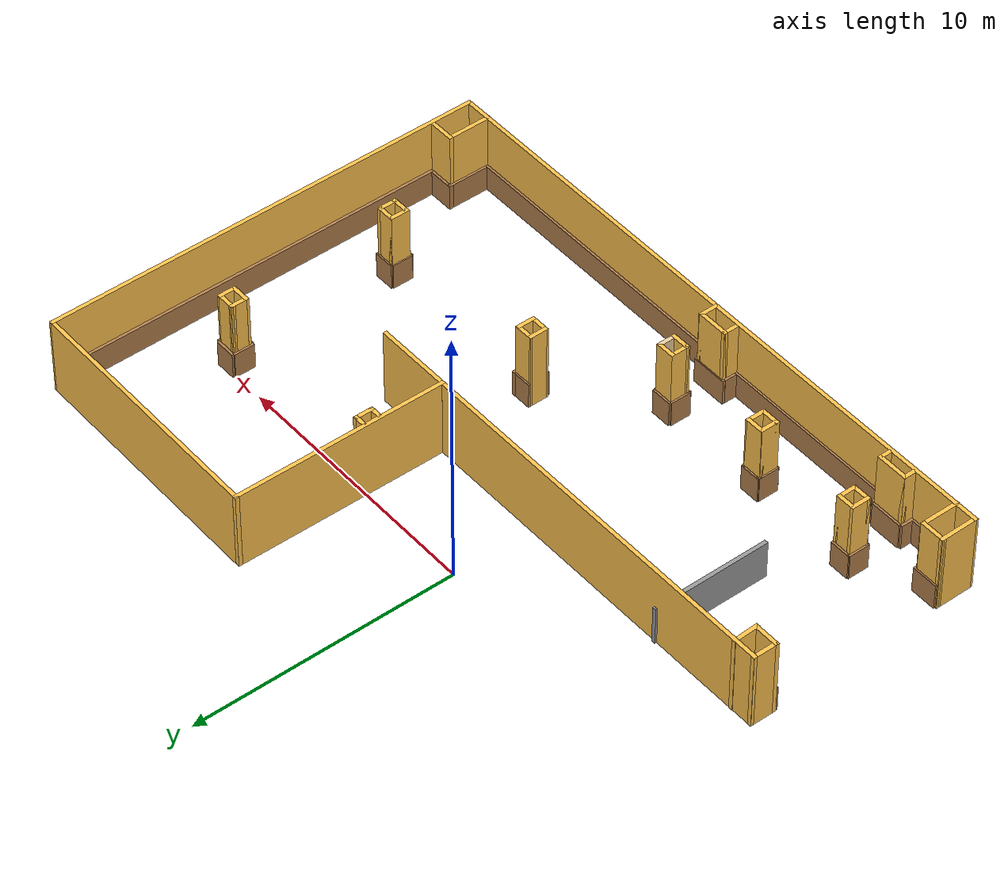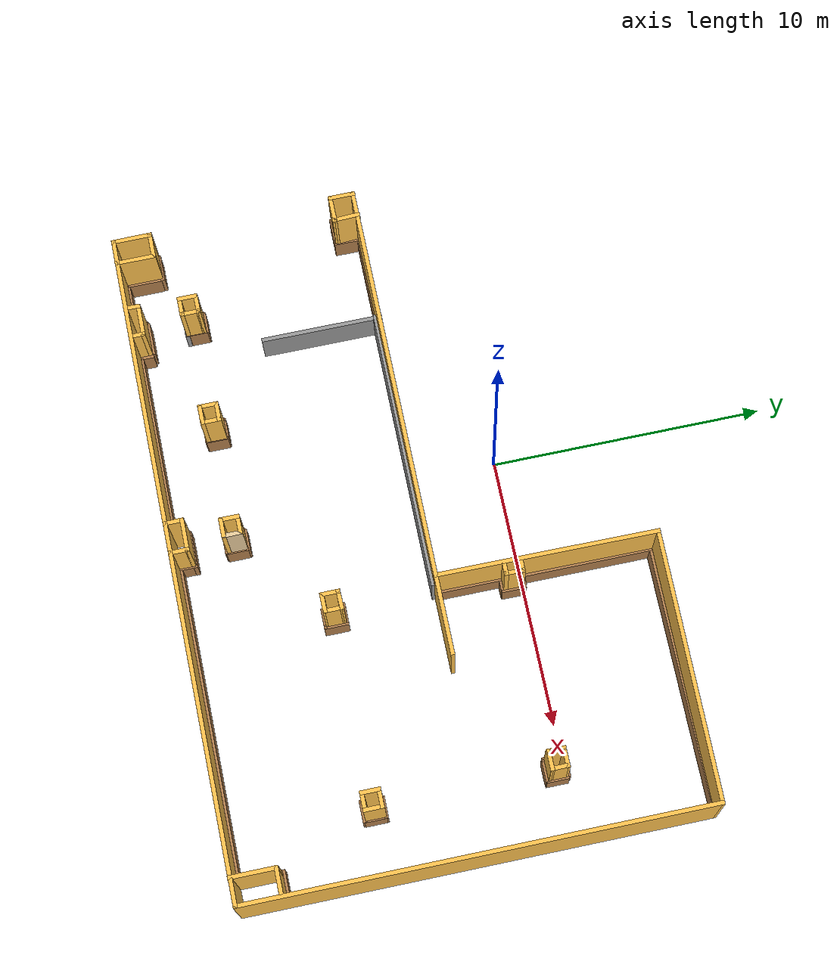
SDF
<?xml version='1.0'?>
<sdf version='1.6'>
  <model name='costa-gv'>
    <pose frame=''>1.97685 -3.58664 0 0 -0 0</pose>
    <link name='Wall_10'>
      <collision name='Wall_10_Collision'>
        <geometry>
          <box>
            <size>15 0.15 3</size>
          </box>
        </geometry>
        <pose frame=''>0 0 1.5 0 -0 0</pose>
      </collision>
      <visual name='Wall_10_Visual'>
        <pose frame=''>0 0 1.5 0 -0 0</pose>
        <geometry>
          <box>
            <size>15 0.15 3</size>
          </box>
        </geometry>
        <material>
          <script>
            <uri>file://media/materials/scripts/gazebo.material</uri>
            <name>Gazebo/Grey</name>
          </script>
          <ambient>1 0.764706 0.305882 1</ambient>
        </material>
        <meta>
          <layer>0</layer>
        </meta>
      </visual>
      <pose frame=''>-4.93585 0.471568 0 0 -0 -3.14024</pose>
    </link>
    <link name='Wall_103'>
      <collision name='Wall_103_Collision'>
        <geometry>
          <box>
            <size>3.4811 0.15 1</size>
          </box>
        </geometry>
        <pose frame=''>0 0 0.5 0 -0 0</pose>
      </collision>
      <visual name='Wall_103_Visual'>
        <pose frame=''>0 0 0.5 0 -0 0</pose>
        <geometry>
          <box>
            <size>3.4811 0.15 1</size>
          </box>
        </geometry>
        <material>
          <script>
            <uri>file://media/materials/scripts/gazebo.material</uri>
            <name>Gazebo/Wood</name>
          </script>
          <ambient>1 1 1 1</ambient>
        </material>
        <meta>
          <layer>0</layer>
        </meta>
      </visual>
      <pose frame=''>-9.76907 0.427453 0 0 -0 3.14152</pose>
    </link>
    <link name='Wall_108'>
      <collision name='Wall_108_Collision'>
        <geometry>
          <box>
            <size>1 0.15 1</size>
          </box>
        </geometry>
        <pose frame=''>0 0 0.5 0 -0 0</pose>
      </collision>
      <visual name='Wall_108_Visual'>
        <pose frame=''>0 0 0.5 0 -0 0</pose>
        <geometry>
          <box>
            <size>1 0.15 1</size>
          </box>
        </geometry>
        <material>
          <script>
            <uri>file://media/materials/scripts/gazebo.material</uri>
            <name>Gazebo/Wood</name>
          </script>
          <ambient>1 1 1 1</ambient>
        </material>
        <meta>
          <layer>0</layer>
        </meta>
      </visual>
      <pose frame=''>-11.4344 -0.007502 0 0 -0 -1.5708</pose>
    </link>
    <link name='Wall_117'>
      <collision name='Wall_117_Collision'>
        <geometry>
          <box>
            <size>1 0.15 1</size>
          </box>
        </geometry>
        <pose frame=''>0 0 0.5 0 -0 0</pose>
      </collision>
      <visual name='Wall_117_Visual'>
        <pose frame=''>0 0 0.5 0 -0 0</pose>
        <geometry>
          <box>
            <size>1 0.15 1</size>
          </box>
        </geometry>
        <material>
          <script>
            <uri>file://media/materials/scripts/gazebo.material</uri>
            <name>Gazebo/Wood</name>
          </script>
          <ambient>1 1 1 1</ambient>
        </material>
        <meta>
          <layer>0</layer>
        </meta>
      </visual>
      <pose frame=''>-11.9319 -0.439362 0 0 -0 0</pose>
    </link>
    <link name='Wall_122'>
      <collision name='Wall_122_Collision'>
        <geometry>
          <box>
            <size>1 0.15 1</size>
          </box>
        </geometry>
        <pose frame=''>0 0 0.5 0 -0 0</pose>
      </collision>
      <visual name='Wall_122_Visual'>
        <pose frame=''>0 0 0.5 0 -0 0</pose>
        <geometry>
          <box>
            <size>1 0.15 1</size>
          </box>
        </geometry>
        <material>
          <script>
            <uri>file://media/materials/scripts/gazebo.material</uri>
            <name>Gazebo/Wood</name>
          </script>
          <ambient>1 1 1 1</ambient>
        </material>
        <meta>
          <layer>0</layer>
        </meta>
      </visual>
      <pose frame=''>-11.8018 -7.05636 0 0 -0 0</pose>
    </link>
    <link name='Wall_124'>
      <collision name='Wall_124_Collision'>
        <geometry>
          <box>
            <size>1.25 0.15 1</size>
          </box>
        </geometry>
        <pose frame=''>0 0 0.5 0 -0 0</pose>
      </collision>
      <visual name='Wall_124_Visual'>
        <pose frame=''>0 0 0.5 0 -0 0</pose>
        <geometry>
          <box>
            <size>1.25 0.15 1</size>
          </box>
        </geometry>
        <material>
          <script>
            <uri>file://media/materials/scripts/gazebo.material</uri>
            <name>Gazebo/Wood</name>
          </script>
          <ambient>1 1 1 1</ambient>
        </material>
        <meta>
          <layer>0</layer>
        </meta>
      </visual>
      <pose frame=''>-11.3608 -7.72636 0 0 -0 -1.5708</pose>
    </link>
    <link name='Wall_126'>
      <collision name='Wall_126_Collision'>
        <geometry>
          <box>
            <size>1.75 0.15 1</size>
          </box>
        </geometry>
        <pose frame=''>0 0 0.5 0 -0 0</pose>
      </collision>
      <visual name='Wall_126_Visual'>
        <pose frame=''>0 0 0.5 0 -0 0</pose>
        <geometry>
          <box>
            <size>1.75 0.15 1</size>
          </box>
        </geometry>
        <material>
          <script>
            <uri>file://media/materials/scripts/gazebo.material</uri>
            <name>Gazebo/Wood</name>
          </script>
          <ambient>1 1 1 1</ambient>
        </material>
        <meta>
          <layer>0</layer>
        </meta>
      </visual>
      <pose frame=''>-10.5508 -8.37536 0 0 -0 0</pose>
    </link>
    <link name='Wall_128'>
      <collision name='Wall_128_Collision'>
        <geometry>
          <box>
            <size>1.25 0.15 1</size>
          </box>
        </geometry>
        <pose frame=''>0 0 0.5 0 -0 0</pose>
      </collision>
      <visual name='Wall_128_Visual'>
        <pose frame=''>0 0 0.5 0 -0 0</pose>
        <geometry>
          <box>
            <size>1.25 0.15 1</size>
          </box>
        </geometry>
        <material>
          <script>
            <uri>file://media/materials/scripts/gazebo.material</uri>
            <name>Gazebo/Wood</name>
          </script>
          <ambient>1 1 1 1</ambient>
        </material>
        <meta>
          <layer>0</layer>
        </meta>
      </visual>
      <pose frame=''>-9.08885 -7.91136 0 0 -0 0</pose>
    </link>
    <link name='Wall_130'>
      <collision name='Wall_130_Collision'>
        <geometry>
          <box>
            <size>0.5 0.15 1</size>
          </box>
        </geometry>
        <pose frame=''>0 0 0.5 0 -0 0</pose>
      </collision>
      <visual name='Wall_130_Visual'>
        <pose frame=''>0 0 0.5 0 -0 0</pose>
        <geometry>
          <box>
            <size>0.5 0.15 1</size>
          </box>
        </geometry>
        <material>
          <script>
            <uri>file://media/materials/scripts/gazebo.material</uri>
            <name>Gazebo/Wood</name>
          </script>
          <ambient>1 1 1 1</ambient>
        </material>
        <meta>
          <layer>0</layer>
        </meta>
      </visual>
      <pose frame=''>-8.42085 -8.15736 0 0 -0 -1.5708</pose>
    </link>
    <link name='Wall_132'>
      <collision name='Wall_132_Collision'>
        <geometry>
          <box>
            <size>0.5 0.15 1</size>
          </box>
        </geometry>
        <pose frame=''>0 0 0.5 0 -0 0</pose>
      </collision>
      <visual name='Wall_132_Visual'>
        <pose frame=''>0 0 0.5 0 -0 0</pose>
        <geometry>
          <box>
            <size>0.5 0.15 1</size>
          </box>
        </geometry>
        <material>
          <script>
            <uri>file://media/materials/scripts/gazebo.material</uri>
            <name>Gazebo/Wood</name>
          </script>
          <ambient>1 1 1 1</ambient>
        </material>
        <meta>
          <layer>0</layer>
        </meta>
      </visual>
      <pose frame=''>-9.72985 -8.13736 0 0 -0 -1.5708</pose>
    </link>
    <link name='Wall_134'>
      <collision name='Wall_134_Collision'>
        <geometry>
          <box>
            <size>7 0.15 1</size>
          </box>
        </geometry>
        <pose frame=''>0 0 0.5 0 -0 0</pose>
      </collision>
      <visual name='Wall_134_Visual'>
        <pose frame=''>0 0 0.5 0 -0 0</pose>
        <geometry>
          <box>
            <size>7 0.15 1</size>
          </box>
        </geometry>
        <material>
          <script>
            <uri>file://media/materials/scripts/gazebo.material</uri>
            <name>Gazebo/Wood</name>
          </script>
          <ambient>1 1 1 1</ambient>
        </material>
        <meta>
          <layer>0</layer>
        </meta>
      </visual>
      <pose frame=''>-4.89485 -8.37536 0 0 -0 0</pose>
    </link>
    <link name='Wall_137'>
      <collision name='Wall_137_Collision'>
        <geometry>
          <box>
            <size>0.5 0.15 1</size>
          </box>
        </geometry>
        <pose frame=''>0 0 0.5 0 -0 0</pose>
      </collision>
      <visual name='Wall_137_Visual'>
        <pose frame=''>0 0 0.5 0 -0 0</pose>
        <geometry>
          <box>
            <size>0.5 0.15 1</size>
          </box>
        </geometry>
        <material>
          <script>
            <uri>file://media/materials/scripts/gazebo.material</uri>
            <name>Gazebo/Wood</name>
          </script>
          <ambient>1 1 1 1</ambient>
        </material>
        <meta>
          <layer>0</layer>
        </meta>
      </visual>
      <pose frame=''>-1.42185 -8.07636 0 0 -0 -1.5708</pose>
    </link>
    <link name='Wall_141'>
      <collision name='Wall_141_Collision'>
        <geometry>
          <box>
            <size>0.8 0.15 1</size>
          </box>
        </geometry>
        <pose frame=''>0 0 0.5 0 -0 0</pose>
      </collision>
      <visual name='Wall_141_Visual'>
        <pose frame=''>0 0 0.5 0 -0 0</pose>
        <geometry>
          <box>
            <size>0.8 0.15 1</size>
          </box>
        </geometry>
        <material>
          <script>
            <uri>file://media/materials/scripts/gazebo.material</uri>
            <name>Gazebo/Grey</name>
          </script>
          <ambient>1 1 1 1</ambient>
        </material>
        <meta>
          <layer>0</layer>
        </meta>
      </visual>
      <pose frame=''>-9.29371 -6.54229 0 0 -0 0</pose>
    </link>
    <link name='Wall_146'>
      <collision name='Wall_146_Collision'>
        <geometry>
          <box>
            <size>0.8 0.15 1</size>
          </box>
        </geometry>
        <pose frame=''>0 0 0.5 0 -0 0</pose>
      </collision>
      <visual name='Wall_146_Visual'>
        <pose frame=''>0 0 0.5 0 -0 0</pose>
        <geometry>
          <box>
            <size>0.8 0.15 1</size>
          </box>
        </geometry>
        <material>
          <script>
            <uri>file://media/materials/scripts/gazebo.material</uri>
            <name>Gazebo/Wood</name>
          </script>
          <ambient>1 1 1 1</ambient>
        </material>
        <meta>
          <layer>0</layer>
        </meta>
      </visual>
      <pose frame=''>-9.30375 -5.81726 0 0 -0 0</pose>
    </link>
    <link name='Wall_148'>
      <collision name='Wall_148_Collision'>
        <geometry>
          <box>
            <size>0.8 0.15 1</size>
          </box>
        </geometry>
        <pose frame=''>0 0 0.5 0 -0 0</pose>
      </collision>
      <visual name='Wall_148_Visual'>
        <pose frame=''>0 0 0.5 0 -0 0</pose>
        <geometry>
          <box>
            <size>0.8 0.15 1</size>
          </box>
        </geometry>
        <material>
          <script>
            <uri>file://media/materials/scripts/gazebo.material</uri>
            <name>Gazebo/Wood</name>
          </script>
          <ambient>1 1 1 1</ambient>
        </material>
        <meta>
          <layer>0</layer>
        </meta>
      </visual>
      <pose frame=''>-8.9742 -6.19261 0 0 -0 -1.5708</pose>
    </link>
    <link name='Wall_150'>
      <collision name='Wall_150_Collision'>
        <geometry>
          <box>
            <size>0.8 0.15 1</size>
          </box>
        </geometry>
        <pose frame=''>0 0 0.5 0 -0 0</pose>
      </collision>
      <visual name='Wall_150_Visual'>
        <pose frame=''>0 0 0.5 0 -0 0</pose>
        <geometry>
          <box>
            <size>0.8 0.15 1</size>
          </box>
        </geometry>
        <material>
          <script>
            <uri>file://media/materials/scripts/gazebo.material</uri>
            <name>Gazebo/Wood</name>
          </script>
          <ambient>1 1 1 1</ambient>
        </material>
        <meta>
          <layer>0</layer>
        </meta>
      </visual>
      <pose frame=''>-9.66903 -6.18254 0 0 -0 -1.5708</pose>
    </link>
    <link name='Wall_152'>
      <collision name='Wall_152_Collision'>
        <geometry>
          <box>
            <size>0.8 0.15 1</size>
          </box>
        </geometry>
        <pose frame=''>0 0 0.5 0 -0 0</pose>
      </collision>
      <visual name='Wall_152_Visual'>
        <pose frame=''>0 0 0.5 0 -0 0</pose>
        <geometry>
          <box>
            <size>0.8 0.15 1</size>
          </box>
        </geometry>
        <material>
          <script>
            <uri>file://media/materials/scripts/gazebo.material</uri>
            <name>Gazebo/Wood</name>
          </script>
          <ambient>1 1 1 1</ambient>
        </material>
        <meta>
          <layer>0</layer>
        </meta>
      </visual>
      <pose frame=''>-5.07028 -6.54841 0 0 -0 0</pose>
    </link>
    <link name='Wall_154'>
      <collision name='Wall_154_Collision'>
        <geometry>
          <box>
            <size>0.8 0.15 1</size>
          </box>
        </geometry>
        <pose frame=''>0 0 0.5 0 -0 0</pose>
      </collision>
      <visual name='Wall_154_Visual'>
        <pose frame=''>0 0 0.5 0 -0 0</pose>
        <geometry>
          <box>
            <size>0.8 0.15 1</size>
          </box>
        </geometry>
        <material>
          <script>
            <uri>file://media/materials/scripts/gazebo.material</uri>
            <name>Gazebo/Wood</name>
          </script>
          <ambient>1 1 1 1</ambient>
        </material>
        <meta>
          <layer>0</layer>
        </meta>
      </visual>
      <pose frame=''>-5.07028 -5.82927 0 0 -0 0</pose>
    </link>
    <link name='Wall_156'>
      <collision name='Wall_156_Collision'>
        <geometry>
          <box>
            <size>0.8 0.15 1</size>
          </box>
        </geometry>
        <pose frame=''>0 0 0.5 0 -0 0</pose>
      </collision>
      <visual name='Wall_156_Visual'>
        <pose frame=''>0 0 0.5 0 -0 0</pose>
        <geometry>
          <box>
            <size>0.8 0.15 1</size>
          </box>
        </geometry>
        <material>
          <script>
            <uri>file://media/materials/scripts/gazebo.material</uri>
            <name>Gazebo/Wood</name>
          </script>
          <ambient>1 1 1 1</ambient>
        </material>
        <meta>
          <layer>0</layer>
        </meta>
      </visual>
      <pose frame=''>-4.7294 -6.19422 0 0 -0 -1.5708</pose>
    </link>
    <link name='Wall_158'>
      <collision name='Wall_158_Collision'>
        <geometry>
          <box>
            <size>0.8 0.15 1</size>
          </box>
        </geometry>
        <pose frame=''>0 0 0.5 0 -0 0</pose>
      </collision>
      <visual name='Wall_158_Visual'>
        <pose frame=''>0 0 0.5 0 -0 0</pose>
        <geometry>
          <box>
            <size>0.8 0.15 1</size>
          </box>
        </geometry>
        <material>
          <script>
            <uri>file://media/materials/scripts/gazebo.material</uri>
            <name>Gazebo/Wood</name>
          </script>
          <ambient>1 1 1 1</ambient>
        </material>
        <meta>
          <layer>0</layer>
        </meta>
      </visual>
      <pose frame=''>-5.42191 -6.19422 0 0 -0 -1.5708</pose>
    </link>
    <link name='Wall_160'>
      <collision name='Wall_160_Collision'>
        <geometry>
          <box>
            <size>1.4 0.15 1</size>
          </box>
        </geometry>
        <pose frame=''>0 0 0.5 0 -0 0</pose>
      </collision>
      <visual name='Wall_160_Visual'>
        <pose frame=''>0 0 0.5 0 -0 0</pose>
        <geometry>
          <box>
            <size>1.4 0.15 1</size>
          </box>
        </geometry>
        <material>
          <script>
            <uri>file://media/materials/scripts/gazebo.material</uri>
            <name>Gazebo/Wood</name>
          </script>
          <ambient>1 1 1 1</ambient>
        </material>
        <meta>
          <layer>0</layer>
        </meta>
      </visual>
      <pose frame=''>-0.788355 -7.81357 0 0 -0 0</pose>
    </link>
    <link name='Wall_162'>
      <collision name='Wall_162_Collision'>
        <geometry>
          <box>
            <size>0.7 0.15 1</size>
          </box>
        </geometry>
        <pose frame=''>0 0 0.5 0 -0 0</pose>
      </collision>
      <visual name='Wall_162_Visual'>
        <pose frame=''>0 0 0.5 0 -0 0</pose>
        <geometry>
          <box>
            <size>0.7 0.15 1</size>
          </box>
        </geometry>
        <material>
          <script>
            <uri>file://media/materials/scripts/gazebo.material</uri>
            <name>Gazebo/Wood</name>
          </script>
          <ambient>1 1 1 1</ambient>
        </material>
        <meta>
          <layer>0</layer>
        </meta>
      </visual>
      <pose frame=''>-0.174848 -8.16836 0 0 -0 -1.5708</pose>
    </link>
    <link name='Wall_167'>
      <collision name='Wall_167_Collision'>
        <geometry>
          <box>
            <size>0.8 0.15 1</size>
          </box>
        </geometry>
        <pose frame=''>0 0 0.5 0 -0 0</pose>
      </collision>
      <visual name='Wall_167_Visual'>
        <pose frame=''>0 0 0.5 0 -0 0</pose>
        <geometry>
          <box>
            <size>0.8 0.15 1</size>
          </box>
        </geometry>
        <material>
          <script>
            <uri>file://media/materials/scripts/gazebo.material</uri>
            <name>Gazebo/Wood</name>
          </script>
          <ambient>1 1 1 1</ambient>
        </material>
        <meta>
          <layer>0</layer>
        </meta>
      </visual>
      <pose frame=''>-1.13366 -6.23417 0 0 -0 -1.5708</pose>
    </link>
    <link name='Wall_169'>
      <collision name='Wall_169_Collision'>
        <geometry>
          <box>
            <size>0.8 0.15 1</size>
          </box>
        </geometry>
        <pose frame=''>0 0 0.5 0 -0 0</pose>
      </collision>
      <visual name='Wall_169_Visual'>
        <pose frame=''>0 0 0.5 0 -0 0</pose>
        <geometry>
          <box>
            <size>0.8 0.15 1</size>
          </box>
        </geometry>
        <material>
          <script>
            <uri>file://media/materials/scripts/gazebo.material</uri>
            <name>Gazebo/Wood</name>
          </script>
          <ambient>1 1 1 1</ambient>
        </material>
        <meta>
          <layer>0</layer>
        </meta>
      </visual>
      <pose frame=''>-0.414512 -6.23417 0 0 -0 -1.5708</pose>
    </link>
    <link name='Wall_171'>
      <collision name='Wall_171_Collision'>
        <geometry>
          <box>
            <size>0.8 0.15 1</size>
          </box>
        </geometry>
        <pose frame=''>0 0 0.5 0 -0 0</pose>
      </collision>
      <visual name='Wall_171_Visual'>
        <pose frame=''>0 0 0.5 0 -0 0</pose>
        <geometry>
          <box>
            <size>0.8 0.15 1</size>
          </box>
        </geometry>
        <material>
          <script>
            <uri>file://media/materials/scripts/gazebo.material</uri>
            <name>Gazebo/Wood</name>
          </script>
          <ambient>1 1 1 1</ambient>
        </material>
        <meta>
          <layer>0</layer>
        </meta>
      </visual>
      <pose frame=''>-0.768707 -6.60168 0 0 -0 0</pose>
    </link>
    <link name='Wall_173'>
      <collision name='Wall_173_Collision'>
        <geometry>
          <box>
            <size>0.8 0.15 1</size>
          </box>
        </geometry>
        <pose frame=''>0 0 0.5 0 -0 0</pose>
      </collision>
      <visual name='Wall_173_Visual'>
        <pose frame=''>0 0 0.5 0 -0 0</pose>
        <geometry>
          <box>
            <size>0.8 0.15 1</size>
          </box>
        </geometry>
        <material>
          <script>
            <uri>file://media/materials/scripts/gazebo.material</uri>
            <name>Gazebo/Wood</name>
          </script>
          <ambient>1 1 1 1</ambient>
        </material>
        <meta>
          <layer>0</layer>
        </meta>
      </visual>
      <pose frame=''>-0.75539 -5.84258 0 0 -0 0</pose>
    </link>
    <link name='Wall_175'>
      <collision name='Wall_175_Collision'>
        <geometry>
          <box>
            <size>11.5 0.15 1</size>
          </box>
        </geometry>
        <pose frame=''>0 0 0.5 0 -0 0</pose>
      </collision>
      <visual name='Wall_175_Visual'>
        <pose frame=''>0 0 0.5 0 -0 0</pose>
        <geometry>
          <box>
            <size>11.5 0.15 1</size>
          </box>
        </geometry>
        <material>
          <script>
            <uri>file://media/materials/scripts/gazebo.material</uri>
            <name>Gazebo/Wood</name>
          </script>
          <ambient>1 1 1 1</ambient>
        </material>
        <meta>
          <layer>0</layer>
        </meta>
      </visual>
      <pose frame=''>5.58313 -8.36284 0 0 -0 0</pose>
    </link>
    <link name='Wall_177'>
      <collision name='Wall_177_Collision'>
        <geometry>
          <box>
            <size>1.6 0.15 1</size>
          </box>
        </geometry>
        <pose frame=''>0 0 0.5 0 -0 0</pose>
      </collision>
      <visual name='Wall_177_Visual'>
        <pose frame=''>0 0 0.5 0 -0 0</pose>
        <geometry>
          <box>
            <size>1.6 0.15 1</size>
          </box>
        </geometry>
        <material>
          <script>
            <uri>file://media/materials/scripts/gazebo.material</uri>
            <name>Gazebo/Wood</name>
          </script>
          <ambient>1 1 1 1</ambient>
        </material>
        <meta>
          <layer>0</layer>
        </meta>
      </visual>
      <pose frame=''>11.2848 -7.54313 0 0 -0 -1.5708</pose>
    </link>
    <link name='Wall_179'>
      <collision name='Wall_179_Collision'>
        <geometry>
          <box>
            <size>1.15 0.15 1</size>
          </box>
        </geometry>
        <pose frame=''>0 0 0.5 0 -0 0</pose>
      </collision>
      <visual name='Wall_179_Visual'>
        <pose frame=''>0 0 0.5 0 -0 0</pose>
        <geometry>
          <box>
            <size>1.15 0.15 1</size>
          </box>
        </geometry>
        <material>
          <script>
            <uri>file://media/materials/scripts/gazebo.material</uri>
            <name>Gazebo/Wood</name>
          </script>
          <ambient>1 1 1 1</ambient>
        </material>
        <meta>
          <layer>0</layer>
        </meta>
      </visual>
      <pose frame=''>11.7805 -6.77121 0 0 -0 3.14159</pose>
    </link>
    <link name='Wall_181'>
      <collision name='Wall_181_Collision'>
        <geometry>
          <box>
            <size>0.75 0.15 1</size>
          </box>
        </geometry>
        <pose frame=''>0 0 0.5 0 -0 0</pose>
      </collision>
      <visual name='Wall_181_Visual'>
        <pose frame=''>0 0 0.5 0 -0 0</pose>
        <geometry>
          <box>
            <size>0.75 0.15 1</size>
          </box>
        </geometry>
        <material>
          <script>
            <uri>file://media/materials/scripts/gazebo.material</uri>
            <name>Gazebo/Wood</name>
          </script>
          <ambient>1 1 1 1</ambient>
        </material>
        <meta>
          <layer>0</layer>
        </meta>
      </visual>
      <pose frame=''>2.70847 -3.64523 0 0 -0 0</pose>
    </link>
    <link name='Wall_183'>
      <collision name='Wall_183_Collision'>
        <geometry>
          <box>
            <size>0.9 0.15 1</size>
          </box>
        </geometry>
        <pose frame=''>0 0 0.5 0 -0 0</pose>
      </collision>
      <visual name='Wall_183_Visual'>
        <pose frame=''>0 0 0.5 0 -0 0</pose>
        <geometry>
          <box>
            <size>0.9 0.15 1</size>
          </box>
        </geometry>
        <material>
          <script>
            <uri>file://media/materials/scripts/gazebo.material</uri>
            <name>Gazebo/Wood</name>
          </script>
          <ambient>1 1 1 1</ambient>
        </material>
        <meta>
          <layer>0</layer>
        </meta>
      </visual>
      <pose frame=''>3.03515 -3.27436 0 0 -0 -1.5708</pose>
    </link>
    <link name='Wall_185'>
      <collision name='Wall_185_Collision'>
        <geometry>
          <box>
            <size>0.75 0.15 1</size>
          </box>
        </geometry>
        <pose frame=''>0 0 0.5 0 -0 0</pose>
      </collision>
      <visual name='Wall_185_Visual'>
        <pose frame=''>0 0 0.5 0 -0 0</pose>
        <geometry>
          <box>
            <size>0.75 0.15 1</size>
          </box>
        </geometry>
        <material>
          <script>
            <uri>file://media/materials/scripts/gazebo.material</uri>
            <name>Gazebo/Wood</name>
          </script>
          <ambient>1 1 1 1</ambient>
        </material>
        <meta>
          <layer>0</layer>
        </meta>
      </visual>
      <pose frame=''>2.65506 -2.89971 0 0 -0 0</pose>
    </link>
    <link name='Wall_187'>
      <collision name='Wall_187_Collision'>
        <geometry>
          <box>
            <size>0.8 0.15 1</size>
          </box>
        </geometry>
        <pose frame=''>0 0 0.5 0 -0 0</pose>
      </collision>
      <visual name='Wall_187_Visual'>
        <pose frame=''>0 0 0.5 0 -0 0</pose>
        <geometry>
          <box>
            <size>0.8 0.15 1</size>
          </box>
        </geometry>
        <material>
          <script>
            <uri>file://media/materials/scripts/gazebo.material</uri>
            <name>Gazebo/Wood</name>
          </script>
          <ambient>1 1 1 1</ambient>
        </material>
        <meta>
          <layer>0</layer>
        </meta>
      </visual>
      <pose frame=''>10.133 -3.27767 0 0 -0 -1.5708</pose>
    </link>
    <link name='Wall_189'>
      <collision name='Wall_189_Collision'>
        <geometry>
          <box>
            <size>0.8 0.15 1</size>
          </box>
        </geometry>
        <pose frame=''>0 0 0.5 0 -0 0</pose>
      </collision>
      <visual name='Wall_189_Visual'>
        <pose frame=''>0 0 0.5 0 -0 0</pose>
        <geometry>
          <box>
            <size>0.8 0.15 1</size>
          </box>
        </geometry>
        <material>
          <script>
            <uri>file://media/materials/scripts/gazebo.material</uri>
            <name>Gazebo/Wood</name>
          </script>
          <ambient>1 1 1 1</ambient>
        </material>
        <meta>
          <layer>0</layer>
        </meta>
      </visual>
      <pose frame=''>9.42716 -3.27767 0 0 -0 -1.5708</pose>
    </link>
    <link name='Wall_191'>
      <collision name='Wall_191_Collision'>
        <geometry>
          <box>
            <size>0.8 0.15 1</size>
          </box>
        </geometry>
        <pose frame=''>0 0 0.5 0 -0 0</pose>
      </collision>
      <visual name='Wall_191_Visual'>
        <pose frame=''>0 0 0.5 0 -0 0</pose>
        <geometry>
          <box>
            <size>0.8 0.15 1</size>
          </box>
        </geometry>
        <material>
          <script>
            <uri>file://media/materials/scripts/gazebo.material</uri>
            <name>Gazebo/Wood</name>
          </script>
          <ambient>1 1 1 1</ambient>
        </material>
        <meta>
          <layer>0</layer>
        </meta>
      </visual>
      <pose frame=''>9.79211 -2.8994 0 0 -0 0</pose>
    </link>
    <link name='Wall_193'>
      <collision name='Wall_193_Collision'>
        <geometry>
          <box>
            <size>0.8 0.15 1</size>
          </box>
        </geometry>
        <pose frame=''>0 0 0.5 0 -0 0</pose>
      </collision>
      <visual name='Wall_193_Visual'>
        <pose frame=''>0 0 0.5 0 -0 0</pose>
        <geometry>
          <box>
            <size>0.8 0.15 1</size>
          </box>
        </geometry>
        <material>
          <script>
            <uri>file://media/materials/scripts/gazebo.material</uri>
            <name>Gazebo/Wood</name>
          </script>
          <ambient>1 1 1 1</ambient>
        </material>
        <meta>
          <layer>0</layer>
        </meta>
      </visual>
      <pose frame=''>9.79211 -3.6585 0 0 -0 0</pose>
    </link>
    <link name='Wall_195'>
      <collision name='Wall_195_Collision'>
        <geometry>
          <box>
            <size>2.5 0.15 1</size>
          </box>
        </geometry>
        <pose frame=''>0 0 0.5 0 -0 0</pose>
      </collision>
      <visual name='Wall_195_Visual'>
        <pose frame=''>0 0 0.5 0 -0 0</pose>
        <geometry>
          <box>
            <size>2.5 0.15 1</size>
          </box>
        </geometry>
        <material>
          <script>
            <uri>file://media/materials/scripts/gazebo.material</uri>
            <name>Gazebo/Wood</name>
          </script>
          <ambient>1 1 1 1</ambient>
        </material>
        <meta>
          <layer>0</layer>
        </meta>
      </visual>
      <pose frame=''>2.58315 1.69081 0 0 -0 -1.5708</pose>
    </link>
    <link name='Wall_199'>
      <collision name='Wall_199_Collision'>
        <geometry>
          <box>
            <size>0.9 0.15 1</size>
          </box>
        </geometry>
        <pose frame=''>0 0 0.5 0 -0 0</pose>
      </collision>
      <visual name='Wall_199_Visual'>
        <pose frame=''>0 0 0.5 0 -0 0</pose>
        <geometry>
          <box>
            <size>0.9 0.15 1</size>
          </box>
        </geometry>
        <material>
          <script>
            <uri>file://media/materials/scripts/gazebo.material</uri>
            <name>Gazebo/Wood</name>
          </script>
          <ambient>1 1 1 1</ambient>
        </material>
        <meta>
          <layer>0</layer>
        </meta>
      </visual>
      <pose frame=''>3.02615 3.21247 0 0 -0 -1.5708</pose>
    </link>
    <link name='Wall_20'>
      <collision name='Wall_20_Collision'>
        <geometry>
          <box>
            <size>0.75 0.15 3</size>
          </box>
        </geometry>
        <pose frame=''>0 0 1.5 0 -0 0</pose>
      </collision>
      <visual name='Wall_20_Visual'>
        <pose frame=''>0 0 1.5 0 -0 0</pose>
        <geometry>
          <box>
            <size>0.75 0.15 3</size>
          </box>
        </geometry>
        <material>
          <script>
            <uri>file://media/materials/scripts/gazebo.material</uri>
            <name>Gazebo/Grey</name>
          </script>
          <ambient>1 0.764706 0.305882 1</ambient>
        </material>
        <meta>
          <layer>0</layer>
        </meta>
      </visual>
      <pose frame=''>-9.28985 -5.90136 0 0 -0 0</pose>
    </link>
    <link name='Wall_201'>
      <collision name='Wall_201_Collision'>
        <geometry>
          <box>
            <size>0.5 0.15 1</size>
          </box>
        </geometry>
        <pose frame=''>0 0 0.5 0 -0 0</pose>
      </collision>
      <visual name='Wall_201_Visual'>
        <pose frame=''>0 0 0.5 0 -0 0</pose>
        <geometry>
          <box>
            <size>0.5 0.15 1</size>
          </box>
        </geometry>
        <material>
          <script>
            <uri>file://media/materials/scripts/gazebo.material</uri>
            <name>Gazebo/Wood</name>
          </script>
          <ambient>1 1 1 1</ambient>
        </material>
        <meta>
          <layer>0</layer>
        </meta>
      </visual>
      <pose frame=''>2.75815 2.81964 0 0 -0 3.14159</pose>
    </link>
    <link name='Wall_203'>
      <collision name='Wall_203_Collision'>
        <geometry>
          <box>
            <size>0.5 0.15 1</size>
          </box>
        </geometry>
        <pose frame=''>0 0 0.5 0 -0 0</pose>
      </collision>
      <visual name='Wall_203_Visual'>
        <pose frame=''>0 0 0.5 0 -0 0</pose>
        <geometry>
          <box>
            <size>0.5 0.15 1</size>
          </box>
        </geometry>
        <material>
          <script>
            <uri>file://media/materials/scripts/gazebo.material</uri>
            <name>Gazebo/Wood</name>
          </script>
          <ambient>1 1 1 1</ambient>
        </material>
        <meta>
          <layer>0</layer>
        </meta>
      </visual>
      <pose frame=''>2.73412 3.61144 0 0 -0 3.14159</pose>
    </link>
    <link name='Wall_205'>
      <collision name='Wall_205_Collision'>
        <geometry>
          <box>
            <size>4.75 0.15 1</size>
          </box>
        </geometry>
        <pose frame=''>0 0 0.5 0 -0 0</pose>
      </collision>
      <visual name='Wall_205_Visual'>
        <pose frame=''>0 0 0.5 0 -0 0</pose>
        <geometry>
          <box>
            <size>4.75 0.15 1</size>
          </box>
        </geometry>
        <material>
          <script>
            <uri>file://media/materials/scripts/gazebo.material</uri>
            <name>Gazebo/Wood</name>
          </script>
          <ambient>1 1 1 1</ambient>
        </material>
        <meta>
          <layer>0</layer>
        </meta>
      </visual>
      <pose frame=''>2.60715 6.03935 0 0 -0 -1.5708</pose>
    </link>
    <link name='Wall_207'>
      <collision name='Wall_207_Collision'>
        <geometry>
          <box>
            <size>0.8 0.15 1</size>
          </box>
        </geometry>
        <pose frame=''>0 0 0.5 0 -0 0</pose>
      </collision>
      <visual name='Wall_207_Visual'>
        <pose frame=''>0 0 0.5 0 -0 0</pose>
        <geometry>
          <box>
            <size>0.8 0.15 1</size>
          </box>
        </geometry>
        <material>
          <script>
            <uri>file://media/materials/scripts/gazebo.material</uri>
            <name>Gazebo/Wood</name>
          </script>
          <ambient>1 1 1 1</ambient>
        </material>
        <meta>
          <layer>0</layer>
        </meta>
      </visual>
      <pose frame=''>9.6862 3.63471 0 0 -0 0</pose>
    </link>
    <link name='Wall_209'>
      <collision name='Wall_209_Collision'>
        <geometry>
          <box>
            <size>0.8 0.15 1</size>
          </box>
        </geometry>
        <pose frame=''>0 0 0.5 0 -0 0</pose>
      </collision>
      <visual name='Wall_209_Visual'>
        <pose frame=''>0 0 0.5 0 -0 0</pose>
        <geometry>
          <box>
            <size>0.8 0.15 1</size>
          </box>
        </geometry>
        <material>
          <script>
            <uri>file://media/materials/scripts/gazebo.material</uri>
            <name>Gazebo/Wood</name>
          </script>
          <ambient>1 1 1 1</ambient>
        </material>
        <meta>
          <layer>0</layer>
        </meta>
      </visual>
      <pose frame=''>9.70978 2.88914 0 0 -0 0</pose>
    </link>
    <link name='Wall_21'>
      <collision name='Wall_21_Collision'>
        <geometry>
          <box>
            <size>0.75 0.15 3</size>
          </box>
        </geometry>
        <pose frame=''>0 0 1.5 0 -0 0</pose>
      </collision>
      <visual name='Wall_21_Visual'>
        <pose frame=''>0 0 1.5 0 -0 0</pose>
        <geometry>
          <box>
            <size>0.75 0.15 3</size>
          </box>
        </geometry>
        <material>
          <script>
            <uri>file://media/materials/scripts/gazebo.material</uri>
            <name>Gazebo/Grey</name>
          </script>
          <ambient>1 0.764706 0.305882 1</ambient>
        </material>
        <meta>
          <layer>0</layer>
        </meta>
      </visual>
      <pose frame=''>-8.98985 -6.20136 0 0 -0 -1.5708</pose>
    </link>
    <link name='Wall_211'>
      <collision name='Wall_211_Collision'>
        <geometry>
          <box>
            <size>0.8 0.15 1</size>
          </box>
        </geometry>
        <pose frame=''>0 0 0.5 0 -0 0</pose>
      </collision>
      <visual name='Wall_211_Visual'>
        <pose frame=''>0 0 0.5 0 -0 0</pose>
        <geometry>
          <box>
            <size>0.8 0.15 1</size>
          </box>
        </geometry>
        <material>
          <script>
            <uri>file://media/materials/scripts/gazebo.material</uri>
            <name>Gazebo/Wood</name>
          </script>
          <ambient>1 1 1 1</ambient>
        </material>
        <meta>
          <layer>0</layer>
        </meta>
      </visual>
      <pose frame=''>10.0836 3.23963 0 0 -0 -1.5708</pose>
    </link>
    <link name='Wall_213'>
      <collision name='Wall_213_Collision'>
        <geometry>
          <box>
            <size>0.8 0.15 1</size>
          </box>
        </geometry>
        <pose frame=''>0 0 0.5 0 -0 0</pose>
      </collision>
      <visual name='Wall_213_Visual'>
        <pose frame=''>0 0 0.5 0 -0 0</pose>
        <geometry>
          <box>
            <size>0.8 0.15 1</size>
          </box>
        </geometry>
        <material>
          <script>
            <uri>file://media/materials/scripts/gazebo.material</uri>
            <name>Gazebo/Wood</name>
          </script>
          <ambient>1 1 1 1</ambient>
        </material>
        <meta>
          <layer>0</layer>
        </meta>
      </visual>
      <pose frame=''>9.31515 3.23964 0 0 -0 -1.5708</pose>
    </link>
    <link name='Wall_215'>
      <collision name='Wall_215_Collision'>
        <geometry>
          <box>
            <size>9.5 0.15 1</size>
          </box>
        </geometry>
        <pose frame=''>0 0 0.5 0 -0 0</pose>
      </collision>
      <visual name='Wall_215_Visual'>
        <pose frame=''>0 0 0.5 0 -0 0</pose>
        <geometry>
          <box>
            <size>9.5 0.15 1</size>
          </box>
        </geometry>
        <material>
          <script>
            <uri>file://media/materials/scripts/gazebo.material</uri>
            <name>Gazebo/Wood</name>
          </script>
          <ambient>1 1 1 1</ambient>
        </material>
        <meta>
          <layer>0</layer>
        </meta>
      </visual>
      <pose frame=''>7.37515 8.36264 0 0 -0 0</pose>
    </link>
    <link name='Wall_217'>
      <collision name='Wall_217_Collision'>
        <geometry>
          <box>
            <size>15.25 0.15 1</size>
          </box>
        </geometry>
        <pose frame=''>0 0 0.5 0 -0 0</pose>
      </collision>
      <visual name='Wall_217_Visual'>
        <pose frame=''>0 0 0.5 0 -0 0</pose>
        <geometry>
          <box>
            <size>15.25 0.15 1</size>
          </box>
        </geometry>
        <material>
          <script>
            <uri>file://media/materials/scripts/gazebo.material</uri>
            <name>Gazebo/Wood</name>
          </script>
          <ambient>1 1 1 1</ambient>
        </material>
        <meta>
          <layer>0</layer>
        </meta>
      </visual>
      <pose frame=''>12.2443 0.762065 0 0 -0 -1.5708</pose>
    </link>
    <link name='Wall_219'>
      <collision name='Wall_219_Collision'>
        <geometry>
          <box>
            <size>10.5 0.15 2</size>
          </box>
        </geometry>
        <pose frame=''>0 0 1 0 -0 0</pose>
      </collision>
      <visual name='Wall_219_Visual'>
        <pose frame=''>0 0 1 0 -0 0</pose>
        <geometry>
          <box>
            <size>10.5 0.15 2</size>
          </box>
        </geometry>
        <material>
          <script>
            <uri>file://media/materials/scripts/gazebo.material</uri>
            <name>Gazebo/Grey</name>
          </script>
          <ambient>1 1 1 1</ambient>
        </material>
        <meta>
          <layer>0</layer>
        </meta>
      </visual>
      <pose frame=''>-2.66326 0.365931 0 0 -0 3.14159</pose>
    </link>
    <link name='Wall_22'>
      <collision name='Wall_22_Collision'>
        <geometry>
          <box>
            <size>0.75 0.15 3</size>
          </box>
        </geometry>
        <pose frame=''>0 0 1.5 0 -0 0</pose>
      </collision>
      <visual name='Wall_22_Visual'>
        <pose frame=''>0 0 1.5 0 -0 0</pose>
        <geometry>
          <box>
            <size>0.75 0.15 3</size>
          </box>
        </geometry>
        <material>
          <script>
            <uri>file://media/materials/scripts/gazebo.material</uri>
            <name>Gazebo/Grey</name>
          </script>
          <ambient>1 0.764706 0.305882 1</ambient>
        </material>
        <meta>
          <layer>0</layer>
        </meta>
      </visual>
      <pose frame=''>-9.28985 -6.50136 0 0 -0 3.14159</pose>
    </link>
    <link name='Wall_23'>
      <collision name='Wall_23_Collision'>
        <geometry>
          <box>
            <size>0.75 0.15 3</size>
          </box>
        </geometry>
        <pose frame=''>0 0 1.5 0 -0 0</pose>
      </collision>
      <visual name='Wall_23_Visual'>
        <pose frame=''>0 0 1.5 0 -0 0</pose>
        <geometry>
          <box>
            <size>0.75 0.15 3</size>
          </box>
        </geometry>
        <material>
          <script>
            <uri>file://media/materials/scripts/gazebo.material</uri>
            <name>Gazebo/Grey</name>
          </script>
          <ambient>1 0.764706 0.305882 1</ambient>
        </material>
        <meta>
          <layer>0</layer>
        </meta>
      </visual>
      <pose frame=''>-9.58985 -6.20136 0 0 -0 1.5708</pose>
    </link>
    <link name='Wall_25'>
      <collision name='Wall_25_Collision'>
        <geometry>
          <box>
            <size>0.75 0.15 3</size>
          </box>
        </geometry>
        <pose frame=''>0 0 1.5 0 -0 0</pose>
      </collision>
      <visual name='Wall_25_Visual'>
        <pose frame=''>0 0 1.5 0 -0 0</pose>
        <geometry>
          <box>
            <size>0.75 0.15 3</size>
          </box>
        </geometry>
        <material>
          <script>
            <uri>file://media/materials/scripts/gazebo.material</uri>
            <name>Gazebo/Grey</name>
          </script>
          <ambient>1 0.764706 0.305882 1</ambient>
        </material>
        <meta>
          <layer>0</layer>
        </meta>
      </visual>
      <pose frame=''>-5.05985 -5.90136 0 0 -0 0</pose>
    </link>
    <link name='Wall_26'>
      <collision name='Wall_26_Collision'>
        <geometry>
          <box>
            <size>0.75 0.15 3</size>
          </box>
        </geometry>
        <pose frame=''>0 0 1.5 0 -0 0</pose>
      </collision>
      <visual name='Wall_26_Visual'>
        <pose frame=''>0 0 1.5 0 -0 0</pose>
        <geometry>
          <box>
            <size>0.75 0.15 3</size>
          </box>
        </geometry>
        <material>
          <script>
            <uri>file://media/materials/scripts/gazebo.material</uri>
            <name>Gazebo/Grey</name>
          </script>
          <ambient>1 0.764706 0.305882 1</ambient>
        </material>
        <meta>
          <layer>0</layer>
        </meta>
      </visual>
      <pose frame=''>-4.75985 -6.20136 0 0 -0 -1.5708</pose>
    </link>
    <link name='Wall_29'>
      <collision name='Wall_29_Collision'>
        <geometry>
          <box>
            <size>0.75 0.15 3</size>
          </box>
        </geometry>
        <pose frame=''>0 0 1.5 0 -0 0</pose>
      </collision>
      <visual name='Wall_29_Visual'>
        <pose frame=''>0 0 1.5 0 -0 0</pose>
        <geometry>
          <box>
            <size>0.75 0.15 3</size>
          </box>
        </geometry>
        <material>
          <script>
            <uri>file://media/materials/scripts/gazebo.material</uri>
            <name>Gazebo/Grey</name>
          </script>
          <ambient>1 0.764706 0.305882 1</ambient>
        </material>
        <meta>
          <layer>0</layer>
        </meta>
      </visual>
      <pose frame=''>-5.35985 -6.20136 0 0 -0 -1.5708</pose>
    </link>
    <link name='Wall_30'>
      <collision name='Wall_30_Collision'>
        <geometry>
          <box>
            <size>0.75 0.15 3</size>
          </box>
        </geometry>
        <pose frame=''>0 0 1.5 0 -0 0</pose>
      </collision>
      <visual name='Wall_30_Visual'>
        <pose frame=''>0 0 1.5 0 -0 0</pose>
        <geometry>
          <box>
            <size>0.75 0.15 3</size>
          </box>
        </geometry>
        <material>
          <script>
            <uri>file://media/materials/scripts/gazebo.material</uri>
            <name>Gazebo/Grey</name>
          </script>
          <ambient>1 0.764706 0.305882 1</ambient>
        </material>
        <meta>
          <layer>0</layer>
        </meta>
      </visual>
      <pose frame=''>-5.05985 -6.50136 0 0 -0 0</pose>
    </link>
    <link name='Wall_32'>
      <collision name='Wall_32_Collision'>
        <geometry>
          <box>
            <size>0.75 0.15 3</size>
          </box>
        </geometry>
        <pose frame=''>0 0 1.5 0 -0 0</pose>
      </collision>
      <visual name='Wall_32_Visual'>
        <pose frame=''>0 0 1.5 0 -0 0</pose>
        <geometry>
          <box>
            <size>0.75 0.15 3</size>
          </box>
        </geometry>
        <material>
          <script>
            <uri>file://media/materials/scripts/gazebo.material</uri>
            <name>Gazebo/Grey</name>
          </script>
          <ambient>1 0.764706 0.305882 1</ambient>
        </material>
        <meta>
          <layer>0</layer>
        </meta>
      </visual>
      <pose frame=''>-0.759848 -5.92136 0 0 -0 0</pose>
    </link>
    <link name='Wall_33'>
      <collision name='Wall_33_Collision'>
        <geometry>
          <box>
            <size>0.75 0.15 3</size>
          </box>
        </geometry>
        <pose frame=''>0 0 1.5 0 -0 0</pose>
      </collision>
      <visual name='Wall_33_Visual'>
        <pose frame=''>0 0 1.5 0 -0 0</pose>
        <geometry>
          <box>
            <size>0.75 0.15 3</size>
          </box>
        </geometry>
        <material>
          <script>
            <uri>file://media/materials/scripts/gazebo.material</uri>
            <name>Gazebo/Grey</name>
          </script>
          <ambient>0.921569 0.807843 0.615686 1</ambient>
        </material>
        <meta>
          <layer>0</layer>
        </meta>
      </visual>
      <pose frame=''>-0.459848 -6.22136 0 0 -0 -1.5708</pose>
    </link>
    <link name='Wall_34'>
      <collision name='Wall_34_Collision'>
        <geometry>
          <box>
            <size>0.75 0.15 3</size>
          </box>
        </geometry>
        <pose frame=''>0 0 1.5 0 -0 0</pose>
      </collision>
      <visual name='Wall_34_Visual'>
        <pose frame=''>0 0 1.5 0 -0 0</pose>
        <geometry>
          <box>
            <size>0.75 0.15 3</size>
          </box>
        </geometry>
        <material>
          <script>
            <uri>file://media/materials/scripts/gazebo.material</uri>
            <name>Gazebo/Grey</name>
          </script>
          <ambient>1 0.764706 0.305882 1</ambient>
        </material>
        <meta>
          <layer>0</layer>
        </meta>
      </visual>
      <pose frame=''>-0.759848 -6.52136 0 0 -0 3.14159</pose>
    </link>
    <link name='Wall_35'>
      <collision name='Wall_35_Collision'>
        <geometry>
          <box>
            <size>0.75 0.15 3</size>
          </box>
        </geometry>
        <pose frame=''>0 0 1.5 0 -0 0</pose>
      </collision>
      <visual name='Wall_35_Visual'>
        <pose frame=''>0 0 1.5 0 -0 0</pose>
        <geometry>
          <box>
            <size>0.75 0.15 3</size>
          </box>
        </geometry>
        <material>
          <script>
            <uri>file://media/materials/scripts/gazebo.material</uri>
            <name>Gazebo/Grey</name>
          </script>
          <ambient>1 0.764706 0.305882 1</ambient>
        </material>
        <meta>
          <layer>0</layer>
        </meta>
      </visual>
      <pose frame=''>-1.05985 -6.22136 0 0 -0 1.5708</pose>
    </link>
    <link name='Wall_37'>
      <collision name='Wall_37_Collision'>
        <geometry>
          <box>
            <size>0.751 0.15 3</size>
          </box>
        </geometry>
        <pose frame=''>0 0 1.5 0 -0 0</pose>
      </collision>
      <visual name='Wall_37_Visual'>
        <pose frame=''>0 0 1.5 0 -0 0</pose>
        <geometry>
          <box>
            <size>0.751 0.15 3</size>
          </box>
        </geometry>
        <material>
          <script>
            <uri>file://media/materials/scripts/gazebo.material</uri>
            <name>Gazebo/Grey</name>
          </script>
          <ambient>1 0.764706 0.305882 1</ambient>
        </material>
        <meta>
          <layer>0</layer>
        </meta>
      </visual>
      <pose frame=''>2.6549 -2.96586 0 0 -0 0.028256</pose>
    </link>
    <link name='Wall_38'>
      <collision name='Wall_38_Collision'>
        <geometry>
          <box>
            <size>0.73251 0.15 3</size>
          </box>
        </geometry>
        <pose frame=''>0 0 1.5 0 -0 0</pose>
      </collision>
      <visual name='Wall_38_Visual'>
        <pose frame=''>0 0 1.5 0 -0 0</pose>
        <geometry>
          <box>
            <size>0.73251 0.15 3</size>
          </box>
        </geometry>
        <material>
          <script>
            <uri>file://media/materials/scripts/gazebo.material</uri>
            <name>Gazebo/Grey</name>
          </script>
          <ambient>1 0.764706 0.305882 1</ambient>
        </material>
        <meta>
          <layer>0</layer>
        </meta>
      </visual>
      <pose frame=''>2.9554 -3.26611 0 0 -0 -1.57164</pose>
    </link>
    <link name='Wall_39'>
      <collision name='Wall_39_Collision'>
        <geometry>
          <box>
            <size>0.75 0.15 3</size>
          </box>
        </geometry>
        <pose frame=''>0 0 1.5 0 -0 0</pose>
      </collision>
      <visual name='Wall_39_Visual'>
        <pose frame=''>0 0 1.5 0 -0 0</pose>
        <geometry>
          <box>
            <size>0.75 0.15 3</size>
          </box>
        </geometry>
        <material>
          <script>
            <uri>file://media/materials/scripts/gazebo.material</uri>
            <name>Gazebo/Grey</name>
          </script>
          <ambient>1 0.764706 0.305882 1</ambient>
        </material>
        <meta>
          <layer>0</layer>
        </meta>
      </visual>
      <pose frame=''>2.65515 -3.55736 0 0 -0 3.14159</pose>
    </link>
    <link name='Wall_40'>
      <collision name='Wall_40_Collision'>
        <geometry>
          <box>
            <size>0.73251 0.15 3</size>
          </box>
        </geometry>
        <pose frame=''>0 0 1.5 0 -0 0</pose>
      </collision>
      <visual name='Wall_40_Visual'>
        <pose frame=''>0 0 1.5 0 -0 0</pose>
        <geometry>
          <box>
            <size>0.73251 0.15 3</size>
          </box>
        </geometry>
        <material>
          <script>
            <uri>file://media/materials/scripts/gazebo.material</uri>
            <name>Gazebo/Grey</name>
          </script>
          <ambient>1 0.764706 0.305882 1</ambient>
        </material>
        <meta>
          <layer>0</layer>
        </meta>
      </visual>
      <pose frame=''>2.35465 -3.26586 0 0 -0 1.57251</pose>
    </link>
    <link name='Wall_42'>
      <collision name='Wall_42_Collision'>
        <geometry>
          <box>
            <size>0.75 0.15 3</size>
          </box>
        </geometry>
        <pose frame=''>0 0 1.5 0 -0 0</pose>
      </collision>
      <visual name='Wall_42_Visual'>
        <pose frame=''>0 0 1.5 0 -0 0</pose>
        <geometry>
          <box>
            <size>0.75 0.15 3</size>
          </box>
        </geometry>
        <material>
          <script>
            <uri>file://media/materials/scripts/gazebo.material</uri>
            <name>Gazebo/Grey</name>
          </script>
          <ambient>1 0.764706 0.305882 1</ambient>
        </material>
        <meta>
          <layer>0</layer>
        </meta>
      </visual>
      <pose frame=''>9.77815 -2.95836 0 0 -0 0</pose>
    </link>
    <link name='Wall_43'>
      <collision name='Wall_43_Collision'>
        <geometry>
          <box>
            <size>0.75 0.15 3</size>
          </box>
        </geometry>
        <pose frame=''>0 0 1.5 0 -0 0</pose>
      </collision>
      <visual name='Wall_43_Visual'>
        <pose frame=''>0 0 1.5 0 -0 0</pose>
        <geometry>
          <box>
            <size>0.75 0.15 3</size>
          </box>
        </geometry>
        <material>
          <script>
            <uri>file://media/materials/scripts/gazebo.material</uri>
            <name>Gazebo/Grey</name>
          </script>
          <ambient>1 0.764706 0.305882 1</ambient>
        </material>
        <meta>
          <layer>0</layer>
        </meta>
      </visual>
      <pose frame=''>10.0782 -3.25836 0 0 -0 -1.5708</pose>
    </link>
    <link name='Wall_44'>
      <collision name='Wall_44_Collision'>
        <geometry>
          <box>
            <size>0.749866 0.15 3</size>
          </box>
        </geometry>
        <pose frame=''>0 0 1.5 0 -0 0</pose>
      </collision>
      <visual name='Wall_44_Visual'>
        <pose frame=''>0 0 1.5 0 -0 0</pose>
        <geometry>
          <box>
            <size>0.749866 0.15 3</size>
          </box>
        </geometry>
        <material>
          <script>
            <uri>file://media/materials/scripts/gazebo.material</uri>
            <name>Gazebo/Grey</name>
          </script>
          <ambient>1 0.764706 0.305882 1</ambient>
        </material>
        <meta>
          <layer>0</layer>
        </meta>
      </visual>
      <pose frame=''>9.77815 -3.55836 0 0 -0 3.14159</pose>
    </link>
    <link name='Wall_45'>
      <collision name='Wall_45_Collision'>
        <geometry>
          <box>
            <size>0.75 0.15 3</size>
          </box>
        </geometry>
        <pose frame=''>0 0 1.5 0 -0 0</pose>
      </collision>
      <visual name='Wall_45_Visual'>
        <pose frame=''>0 0 1.5 0 -0 0</pose>
        <geometry>
          <box>
            <size>0.75 0.15 3</size>
          </box>
        </geometry>
        <material>
          <script>
            <uri>file://media/materials/scripts/gazebo.material</uri>
            <name>Gazebo/Grey</name>
          </script>
          <ambient>1 0.764706 0.305882 1</ambient>
        </material>
        <meta>
          <layer>0</layer>
        </meta>
      </visual>
      <pose frame=''>9.47815 -3.25836 0 0 -0 1.5708</pose>
    </link>
    <link name='Wall_47'>
      <collision name='Wall_47_Collision'>
        <geometry>
          <box>
            <size>0.5 0.15 3</size>
          </box>
        </geometry>
        <pose frame=''>0 0 1.5 0 -0 0</pose>
      </collision>
      <visual name='Wall_47_Visual'>
        <pose frame=''>0 0 1.5 0 -0 0</pose>
        <geometry>
          <box>
            <size>0.5 0.15 3</size>
          </box>
        </geometry>
        <material>
          <script>
            <uri>file://media/materials/scripts/gazebo.material</uri>
            <name>Gazebo/Grey</name>
          </script>
          <ambient>1 0.764706 0.305882 1</ambient>
        </material>
        <meta>
          <layer>0</layer>
        </meta>
      </visual>
      <pose frame=''>2.77015 3.51064 0 0 -0 0</pose>
    </link>
    <link name='Wall_48'>
      <collision name='Wall_48_Collision'>
        <geometry>
          <box>
            <size>0.75 0.15 3</size>
          </box>
        </geometry>
        <pose frame=''>0 0 1.5 0 -0 0</pose>
      </collision>
      <visual name='Wall_48_Visual'>
        <pose frame=''>0 0 1.5 0 -0 0</pose>
        <geometry>
          <box>
            <size>0.75 0.15 3</size>
          </box>
        </geometry>
        <material>
          <script>
            <uri>file://media/materials/scripts/gazebo.material</uri>
            <name>Gazebo/Grey</name>
          </script>
          <ambient>1 0.764706 0.305882 1</ambient>
        </material>
        <meta>
          <layer>0</layer>
        </meta>
      </visual>
      <pose frame=''>2.94515 3.21064 0 0 -0 -1.5708</pose>
    </link>
    <link name='Wall_49'>
      <collision name='Wall_49_Collision'>
        <geometry>
          <box>
            <size>0.5 0.15 3</size>
          </box>
        </geometry>
        <pose frame=''>0 0 1.5 0 -0 0</pose>
      </collision>
      <visual name='Wall_49_Visual'>
        <pose frame=''>0 0 1.5 0 -0 0</pose>
        <geometry>
          <box>
            <size>0.5 0.15 3</size>
          </box>
        </geometry>
        <material>
          <script>
            <uri>file://media/materials/scripts/gazebo.material</uri>
            <name>Gazebo/Grey</name>
          </script>
          <ambient>1 0.764706 0.305882 1</ambient>
        </material>
        <meta>
          <layer>0</layer>
        </meta>
      </visual>
      <pose frame=''>2.77015 2.91064 0 0 -0 3.14159</pose>
    </link>
    <link name='Wall_52'>
      <collision name='Wall_52_Collision'>
        <geometry>
          <box>
            <size>1.75 0.15 3</size>
          </box>
        </geometry>
        <pose frame=''>0 0 1.5 0 -0 0</pose>
      </collision>
      <visual name='Wall_52_Visual'>
        <pose frame=''>0 0 1.5 0 -0 0</pose>
        <geometry>
          <box>
            <size>1.75 0.15 3</size>
          </box>
        </geometry>
        <material>
          <script>
            <uri>file://media/materials/scripts/gazebo.material</uri>
            <name>Gazebo/Grey</name>
          </script>
          <ambient>1 0.764706 0.305882 1</ambient>
        </material>
        <meta>
          <layer>0</layer>
        </meta>
      </visual>
      <pose frame=''>11.3762 -7.67136 0 0 -0 -1.5708</pose>
    </link>
    <link name='Wall_54'>
      <collision name='Wall_54_Collision'>
        <geometry>
          <box>
            <size>1 0.15 3</size>
          </box>
        </geometry>
        <pose frame=''>0 0 1.5 0 -0 0</pose>
      </collision>
      <visual name='Wall_54_Visual'>
        <pose frame=''>0 0 1.5 0 -0 0</pose>
        <geometry>
          <box>
            <size>1 0.15 3</size>
          </box>
        </geometry>
        <material>
          <script>
            <uri>file://media/materials/scripts/gazebo.material</uri>
            <name>Gazebo/Grey</name>
          </script>
          <ambient>1 0.764706 0.305882 1</ambient>
        </material>
        <meta>
          <layer>0</layer>
        </meta>
      </visual>
      <pose frame=''>11.8012 -6.87136 0 0 -0 0</pose>
    </link>
    <link name='Wall_60'>
      <collision name='Wall_60_Collision'>
        <geometry>
          <box>
            <size>24.796 0.15 3</size>
          </box>
        </geometry>
        <pose frame=''>0 0 1.5 0 -0 0</pose>
      </collision>
      <visual name='Wall_60_Visual'>
        <pose frame=''>0 0 1.5 0 -0 0</pose>
        <geometry>
          <box>
            <size>24.796 0.15 3</size>
          </box>
        </geometry>
        <material>
          <script>
            <uri>file://media/materials/scripts/gazebo.material</uri>
            <name>Gazebo/Grey</name>
          </script>
          <ambient>1 0.764706 0.305882 1</ambient>
        </material>
        <meta>
          <layer>0</layer>
        </meta>
      </visual>
      <pose frame=''>0.037152 -8.45936 0 0 -0 3.14159</pose>
    </link>
    <link name='Wall_62'>
      <collision name='Wall_62_Collision'>
        <geometry>
          <box>
            <size>1.49162 0.15 3</size>
          </box>
        </geometry>
        <pose frame=''>0 0 1.5 0 -0 0</pose>
      </collision>
      <visual name='Wall_62_Visual'>
        <pose frame=''>0 0 1.5 0 -0 0</pose>
        <geometry>
          <box>
            <size>1.49162 0.15 3</size>
          </box>
        </geometry>
        <material>
          <script>
            <uri>file://media/materials/scripts/gazebo.material</uri>
            <name>Gazebo/Grey</name>
          </script>
          <ambient>1 0.764706 0.305882 1</ambient>
        </material>
        <meta>
          <layer>0</layer>
        </meta>
      </visual>
      <pose frame=''>-12.2913 -7.78886 0 0 -0 -1.56259</pose>
    </link>
    <link name='Wall_64'>
      <collision name='Wall_64_Collision'>
        <geometry>
          <box>
            <size>1 0.15 3</size>
          </box>
        </geometry>
        <pose frame=''>0 0 1.5 0 -0 0</pose>
      </collision>
      <visual name='Wall_64_Visual'>
        <pose frame=''>0 0 1.5 0 -0 0</pose>
        <geometry>
          <box>
            <size>1 0.15 3</size>
          </box>
        </geometry>
        <material>
          <script>
            <uri>file://media/materials/scripts/gazebo.material</uri>
            <name>Gazebo/Grey</name>
          </script>
          <ambient>1 0.764706 0.305882 1</ambient>
        </material>
        <meta>
          <layer>0</layer>
        </meta>
      </visual>
      <pose frame=''>-11.8718 -7.11836 0 0 -0 0</pose>
    </link>
    <link name='Wall_65'>
      <collision name='Wall_65_Collision'>
        <geometry>
          <box>
            <size>1.5 0.15 3</size>
          </box>
        </geometry>
        <pose frame=''>0 0 1.5 0 -0 0</pose>
      </collision>
      <visual name='Wall_65_Visual'>
        <pose frame=''>0 0 1.5 0 -0 0</pose>
        <geometry>
          <box>
            <size>1.5 0.15 3</size>
          </box>
        </geometry>
        <material>
          <script>
            <uri>file://media/materials/scripts/gazebo.material</uri>
            <name>Gazebo/Grey</name>
          </script>
          <ambient>1 0.764706 0.305882 1</ambient>
        </material>
        <meta>
          <layer>0</layer>
        </meta>
      </visual>
      <pose frame=''>-11.4468 -7.79336 0 0 -0 -1.5708</pose>
    </link>
    <link name='Wall_67'>
      <collision name='Wall_67_Collision'>
        <geometry>
          <box>
            <size>0.5 0.15 3</size>
          </box>
        </geometry>
        <pose frame=''>0 0 1.5 0 -0 0</pose>
      </collision>
      <visual name='Wall_67_Visual'>
        <pose frame=''>0 0 1.5 0 -0 0</pose>
        <geometry>
          <box>
            <size>0.5 0.15 3</size>
          </box>
        </geometry>
        <material>
          <script>
            <uri>file://media/materials/scripts/gazebo.material</uri>
            <name>Gazebo/Grey</name>
          </script>
          <ambient>1 0.764706 0.305882 1</ambient>
        </material>
        <meta>
          <layer>0</layer>
        </meta>
      </visual>
      <pose frame=''>-9.62785 -8.17636 0 0 -0 1.5708</pose>
    </link>
    <link name='Wall_69'>
      <collision name='Wall_69_Collision'>
        <geometry>
          <box>
            <size>0.15 0.15 2.5</size>
          </box>
        </geometry>
        <pose frame=''>0 0 1.25 0 -0 0</pose>
      </collision>
      <visual name='Wall_69_Visual'>
        <pose frame=''>0 0 1.25 0 -0 0</pose>
        <geometry>
          <box>
            <size>0.15 0.15 2.5</size>
          </box>
        </geometry>
        <material>
          <script>
            <uri>file://media/materials/scripts/gazebo.material</uri>
            <name>Gazebo/Grey</name>
          </script>
          <ambient>1 1 1 1</ambient>
        </material>
        <meta>
          <layer>0</layer>
        </meta>
      </visual>
      <pose frame=''>-8.77792 -8.00156 0 0 -0 0</pose>
    </link>
    <link name='Wall_70'>
      <collision name='Wall_70_Collision'>
        <geometry>
          <box>
            <size>0.15 0.15 2.5</size>
          </box>
        </geometry>
        <pose frame=''>0 0 1.25 0 -0 0</pose>
      </collision>
      <visual name='Wall_70_Visual'>
        <pose frame=''>0 0 1.25 0 -0 0</pose>
        <geometry>
          <box>
            <size>0.15 0.15 2.5</size>
          </box>
        </geometry>
        <material>
          <script>
            <uri>file://media/materials/scripts/gazebo.material</uri>
            <name>Gazebo/Grey</name>
          </script>
          <ambient>1 1 1 1</ambient>
        </material>
        <meta>
          <layer>0</layer>
        </meta>
      </visual>
      <pose frame=''>-8.77792 -8.00156 0 0 -0 0</pose>
    </link>
    <link name='Wall_71'>
      <collision name='Wall_71_Collision'>
        <geometry>
          <box>
            <size>0.15 0.15 2.5</size>
          </box>
        </geometry>
        <pose frame=''>0 0 1.25 0 -0 0</pose>
      </collision>
      <visual name='Wall_71_Visual'>
        <pose frame=''>0 0 1.25 0 -0 0</pose>
        <geometry>
          <box>
            <size>0.15 0.15 2.5</size>
          </box>
        </geometry>
        <material>
          <script>
            <uri>file://media/materials/scripts/gazebo.material</uri>
            <name>Gazebo/Grey</name>
          </script>
          <ambient>1 1 1 1</ambient>
        </material>
        <meta>
          <layer>0</layer>
        </meta>
      </visual>
      <pose frame=''>-8.77792 -8.00156 0 0 -0 0</pose>
    </link>
    <link name='Wall_73'>
      <collision name='Wall_73_Collision'>
        <geometry>
          <box>
            <size>1.25 0.15 3</size>
          </box>
        </geometry>
        <pose frame=''>0 0 1.5 0 -0 0</pose>
      </collision>
      <visual name='Wall_73_Visual'>
        <pose frame=''>0 0 1.5 0 -0 0</pose>
        <geometry>
          <box>
            <size>1.25 0.15 3</size>
          </box>
        </geometry>
        <material>
          <script>
            <uri>file://media/materials/scripts/gazebo.material</uri>
            <name>Gazebo/Grey</name>
          </script>
          <ambient>1 0.764706 0.305882 1</ambient>
        </material>
        <meta>
          <layer>0</layer>
        </meta>
      </visual>
      <pose frame=''>-9.07785 -8.00136 0 0 -0 0</pose>
    </link>
    <link name='Wall_74'>
      <collision name='Wall_74_Collision'>
        <geometry>
          <box>
            <size>0.5 0.15 3</size>
          </box>
        </geometry>
        <pose frame=''>0 0 1.5 0 -0 0</pose>
      </collision>
      <visual name='Wall_74_Visual'>
        <pose frame=''>0 0 1.5 0 -0 0</pose>
        <geometry>
          <box>
            <size>0.5 0.15 3</size>
          </box>
        </geometry>
        <material>
          <script>
            <uri>file://media/materials/scripts/gazebo.material</uri>
            <name>Gazebo/Grey</name>
          </script>
          <ambient>1 0.764706 0.305882 1</ambient>
        </material>
        <meta>
          <layer>0</layer>
        </meta>
      </visual>
      <pose frame=''>-8.52785 -8.17636 0 0 -0 -1.5708</pose>
    </link>
    <link name='Wall_76'>
      <collision name='Wall_76_Collision'>
        <geometry>
          <box>
            <size>0.75 0.15 3</size>
          </box>
        </geometry>
        <pose frame=''>0 0 1.5 0 -0 0</pose>
      </collision>
      <visual name='Wall_76_Visual'>
        <pose frame=''>0 0 1.5 0 -0 0</pose>
        <geometry>
          <box>
            <size>0.75 0.15 3</size>
          </box>
        </geometry>
        <material>
          <script>
            <uri>file://media/materials/scripts/gazebo.material</uri>
            <name>Gazebo/Grey</name>
          </script>
          <ambient>1 0.764706 0.305882 1</ambient>
        </material>
        <meta>
          <layer>0</layer>
        </meta>
      </visual>
      <pose frame=''>-1.33185 -8.15836 0 0 -0 1.5708</pose>
    </link>
    <link name='Wall_77'>
      <collision name='Wall_77_Collision'>
        <geometry>
          <box>
            <size>1.25 0.15 3</size>
          </box>
        </geometry>
        <pose frame=''>0 0 1.5 0 -0 0</pose>
      </collision>
      <visual name='Wall_77_Visual'>
        <pose frame=''>0 0 1.5 0 -0 0</pose>
        <geometry>
          <box>
            <size>1.25 0.15 3</size>
          </box>
        </geometry>
        <material>
          <script>
            <uri>file://media/materials/scripts/gazebo.material</uri>
            <name>Gazebo/Grey</name>
          </script>
          <ambient>1 0.764706 0.305882 1</ambient>
        </material>
        <meta>
          <layer>0</layer>
        </meta>
      </visual>
      <pose frame=''>-0.781848 -7.85836 0 0 -0 0</pose>
    </link>
    <link name='Wall_78'>
      <collision name='Wall_78_Collision'>
        <geometry>
          <box>
            <size>0.75 0.15 3</size>
          </box>
        </geometry>
        <pose frame=''>0 0 1.5 0 -0 0</pose>
      </collision>
      <visual name='Wall_78_Visual'>
        <pose frame=''>0 0 1.5 0 -0 0</pose>
        <geometry>
          <box>
            <size>0.75 0.15 3</size>
          </box>
        </geometry>
        <material>
          <script>
            <uri>file://media/materials/scripts/gazebo.material</uri>
            <name>Gazebo/Grey</name>
          </script>
          <ambient>1 0.764706 0.305882 1</ambient>
        </material>
        <meta>
          <layer>0</layer>
        </meta>
      </visual>
      <pose frame=''>-0.231848 -8.15836 0 0 -0 -1.5708</pose>
    </link>
    <link name='Wall_80'>
      <collision name='Wall_80_Collision'>
        <geometry>
          <box>
            <size>17 0.15 3</size>
          </box>
        </geometry>
        <pose frame=''>0 0 1.5 0 -0 0</pose>
      </collision>
      <visual name='Wall_80_Visual'>
        <pose frame=''>0 0 1.5 0 -0 0</pose>
        <geometry>
          <box>
            <size>17 0.15 3</size>
          </box>
        </geometry>
        <material>
          <script>
            <uri>file://media/materials/scripts/gazebo.material</uri>
            <name>Gazebo/Grey</name>
          </script>
          <ambient>1 0.764706 0.305882 1</ambient>
        </material>
        <meta>
          <layer>0</layer>
        </meta>
      </visual>
      <pose frame=''>12.3602 -0.034362 0 0 -0 1.5708</pose>
    </link>
    <link name='Wall_81'>
      <collision name='Wall_81_Collision'>
        <geometry>
          <box>
            <size>9.97469 0.15 3</size>
          </box>
        </geometry>
        <pose frame=''>0 0 1.5 0 -0 0</pose>
      </collision>
      <visual name='Wall_81_Visual'>
        <pose frame=''>0 0 1.5 0 -0 0</pose>
        <geometry>
          <box>
            <size>9.97469 0.15 3</size>
          </box>
        </geometry>
        <material>
          <script>
            <uri>file://media/materials/scripts/gazebo.material</uri>
            <name>Gazebo/Grey</name>
          </script>
          <ambient>1 0.764706 0.305882 1</ambient>
        </material>
        <meta>
          <layer>0</layer>
        </meta>
      </visual>
      <pose frame=''>7.44815 8.43064 0 0 -0 3.13345</pose>
    </link>
    <link name='Wall_83'>
      <collision name='Wall_83_Collision'>
        <geometry>
          <box>
            <size>0.767 0.15 3</size>
          </box>
        </geometry>
        <pose frame=''>0 0 1.5 0 -0 0</pose>
      </collision>
      <visual name='Wall_83_Visual'>
        <pose frame=''>0 0 1.5 0 -0 0</pose>
        <geometry>
          <box>
            <size>0.767 0.15 3</size>
          </box>
        </geometry>
        <material>
          <script>
            <uri>file://media/materials/scripts/gazebo.material</uri>
            <name>Gazebo/Grey</name>
          </script>
          <ambient>1 0.764706 0.305882 1</ambient>
        </material>
        <meta>
          <layer>0</layer>
        </meta>
      </visual>
      <pose frame=''>9.70765 3.52564 0 0 -0 0</pose>
    </link>
    <link name='Wall_84'>
      <collision name='Wall_84_Collision'>
        <geometry>
          <box>
            <size>0.680042 0.15 3</size>
          </box>
        </geometry>
        <pose frame=''>0 0 1.5 0 -0 0</pose>
      </collision>
      <visual name='Wall_84_Visual'>
        <pose frame=''>0 0 1.5 0 -0 0</pose>
        <geometry>
          <box>
            <size>0.680042 0.15 3</size>
          </box>
        </geometry>
        <material>
          <script>
            <uri>file://media/materials/scripts/gazebo.material</uri>
            <name>Gazebo/Grey</name>
          </script>
          <ambient>1 0.764706 0.305882 1</ambient>
        </material>
        <meta>
          <layer>0</layer>
        </meta>
      </visual>
      <pose frame=''>10.0169 3.26062 0 0 -0 -1.56798</pose>
    </link>
    <link name='Wall_85'>
      <collision name='Wall_85_Collision'>
        <geometry>
          <box>
            <size>0.768 0.15 3</size>
          </box>
        </geometry>
        <pose frame=''>0 0 1.5 0 -0 0</pose>
      </collision>
      <visual name='Wall_85_Visual'>
        <pose frame=''>0 0 1.5 0 -0 0</pose>
        <geometry>
          <box>
            <size>0.768 0.15 3</size>
          </box>
        </geometry>
        <material>
          <script>
            <uri>file://media/materials/scripts/gazebo.material</uri>
            <name>Gazebo/Grey</name>
          </script>
          <ambient>1 0.764706 0.305882 1</ambient>
        </material>
        <meta>
          <layer>0</layer>
        </meta>
      </visual>
      <pose frame=''>9.70864 2.97811 0 0 -0 3.14159</pose>
    </link>
    <link name='Wall_86'>
      <collision name='Wall_86_Collision'>
        <geometry>
          <box>
            <size>0.68004 0.15 3</size>
          </box>
        </geometry>
        <pose frame=''>0 0 1.5 0 -0 0</pose>
      </collision>
      <visual name='Wall_86_Visual'>
        <pose frame=''>0 0 1.5 0 -0 0</pose>
        <geometry>
          <box>
            <size>0.68004 0.15 3</size>
          </box>
        </geometry>
        <material>
          <script>
            <uri>file://media/materials/scripts/gazebo.material</uri>
            <name>Gazebo/Grey</name>
          </script>
          <ambient>1 0.764706 0.305882 1</ambient>
        </material>
        <meta>
          <layer>0</layer>
        </meta>
      </visual>
      <pose frame=''>9.3994 3.26062 0 0 -0 1.57172</pose>
    </link>
    <link name='Wall_88'>
      <collision name='Wall_88_Collision'>
        <geometry>
          <box>
            <size>1 0.15 3</size>
          </box>
        </geometry>
        <pose frame=''>0 0 1.5 0 -0 0</pose>
      </collision>
      <visual name='Wall_88_Visual'>
        <pose frame=''>0 0 1.5 0 -0 0</pose>
        <geometry>
          <box>
            <size>1 0.15 3</size>
          </box>
        </geometry>
        <material>
          <script>
            <uri>file://media/materials/scripts/gazebo.material</uri>
            <name>Gazebo/Grey</name>
          </script>
          <ambient>1 0.764706 0.305882 1</ambient>
        </material>
        <meta>
          <layer>0</layer>
        </meta>
      </visual>
      <pose frame=''>-12.3608 0.046568 0 0 -0 -1.5708</pose>
    </link>
    <link name='Wall_89'>
      <collision name='Wall_89_Collision'>
        <geometry>
          <box>
            <size>1.04028 0.15 3</size>
          </box>
        </geometry>
        <pose frame=''>0 0 1.5 0 -0 0</pose>
      </collision>
      <visual name='Wall_89_Visual'>
        <pose frame=''>0 0 1.5 0 -0 0</pose>
        <geometry>
          <box>
            <size>1.04028 0.15 3</size>
          </box>
        </geometry>
        <material>
          <script>
            <uri>file://media/materials/scripts/gazebo.material</uri>
            <name>Gazebo/Grey</name>
          </script>
          <ambient>1 0.764706 0.305882 1</ambient>
        </material>
        <meta>
          <layer>0</layer>
        </meta>
      </visual>
      <pose frame=''>-11.9157 -0.378432 0 0 -0 0</pose>
    </link>
    <link name='Wall_9'>
      <collision name='Wall_9_Collision'>
        <geometry>
          <box>
            <size>8.13971 0.15 3</size>
          </box>
        </geometry>
        <pose frame=''>0 0 1.5 0 -0 0</pose>
      </collision>
      <visual name='Wall_9_Visual'>
        <pose frame=''>0 0 1.5 0 -0 0</pose>
        <geometry>
          <box>
            <size>8.13971 0.15 3</size>
          </box>
        </geometry>
        <material>
          <script>
            <uri>file://media/materials/scripts/gazebo.material</uri>
            <name>Gazebo/Grey</name>
          </script>
          <ambient>1 0.764706 0.305882 1</ambient>
        </material>
        <meta>
          <layer>0</layer>
        </meta>
      </visual>
      <pose frame=''>2.51265 4.47614 0 0 -0 -1.57668</pose>
    </link>
    <link name='Wall_90'>
      <collision name='Wall_90_Collision'>
        <geometry>
          <box>
            <size>1.02107 0.15 3</size>
          </box>
        </geometry>
        <pose frame=''>0 0 1.5 0 -0 0</pose>
      </collision>
      <visual name='Wall_90_Visual'>
        <pose frame=''>0 0 1.5 0 -0 0</pose>
        <geometry>
          <box>
            <size>1.02107 0.15 3</size>
          </box>
        </geometry>
        <material>
          <script>
            <uri>file://media/materials/scripts/gazebo.material</uri>
            <name>Gazebo/Grey</name>
          </script>
          <ambient>1 0.764706 0.305882 1</ambient>
        </material>
        <meta>
          <layer>0</layer>
        </meta>
      </visual>
      <pose frame=''>-11.4907 0.046568 0 0 -0 1.61705</pose>
    </link>
    <link name='Wall_94'>
      <collision name='Wall_94_Collision'>
        <geometry>
          <box>
            <size>4.5 0.15 1.5</size>
          </box>
        </geometry>
        <pose frame=''>0 0 0.75 0 -0 0</pose>
      </collision>
      <visual name='Wall_94_Visual'>
        <pose frame=''>0 0 0.75 0 -0 0</pose>
        <geometry>
          <box>
            <size>4.5 0.15 1.5</size>
          </box>
        </geometry>
        <material>
          <script>
            <uri>file://media/materials/scripts/gazebo.material</uri>
            <name>Gazebo/Grey</name>
          </script>
          <ambient>0 0 0 1</ambient>
        </material>
        <meta>
          <layer>0</layer>
        </meta>
      </visual>
      <pose frame=''>-7.99085 -1.63536 0 0 -0 -1.5708</pose>
    </link>
    <link name='Wall_98'>
      <collision name='Wall_98_Collision'>
        <geometry>
          <box>
            <size>3 0.15 3</size>
          </box>
        </geometry>
        <pose frame=''>0 0 1.5 0 -0 0</pose>
      </collision>
      <visual name='Wall_98_Visual'>
        <pose frame=''>0 0 1.5 0 -0 0</pose>
        <geometry>
          <box>
            <size>3 0.15 3</size>
          </box>
        </geometry>
        <material>
          <script>
            <uri>file://media/materials/scripts/gazebo.material</uri>
            <name>Gazebo/Grey</name>
          </script>
          <ambient>1 0.764706 0.305882 1</ambient>
        </material>
        <meta>
          <layer>0</layer>
        </meta>
      </visual>
      <pose frame=''>3.91415 0.481638 0 0 -0 0</pose>
    </link>
    <static>1</static>
  </model>
</sdf>
